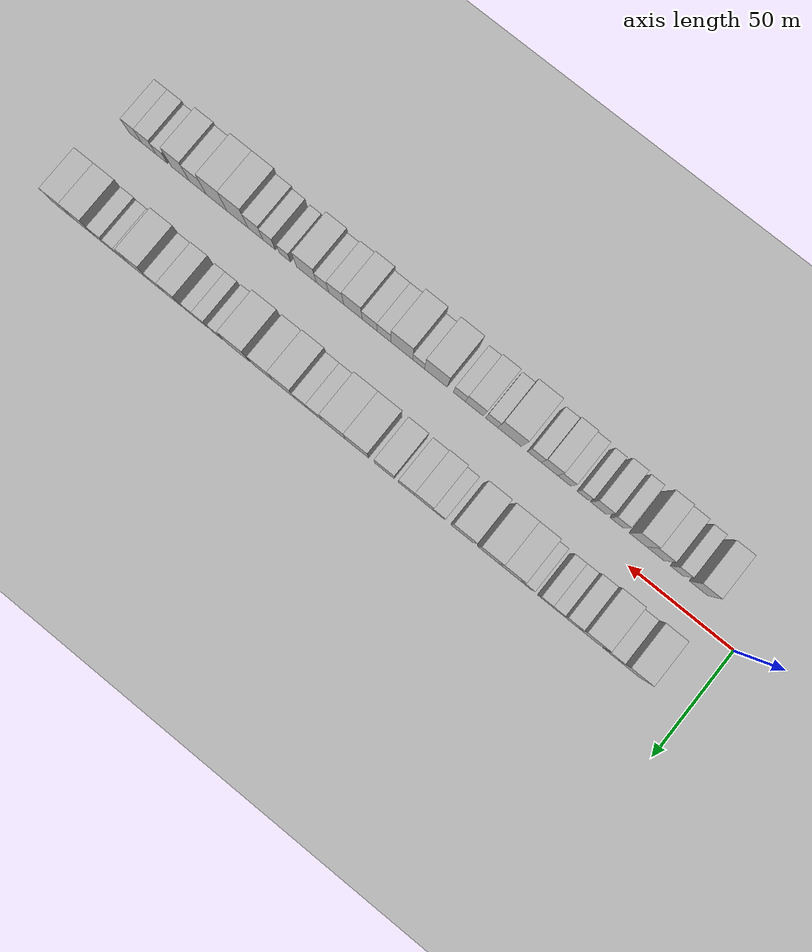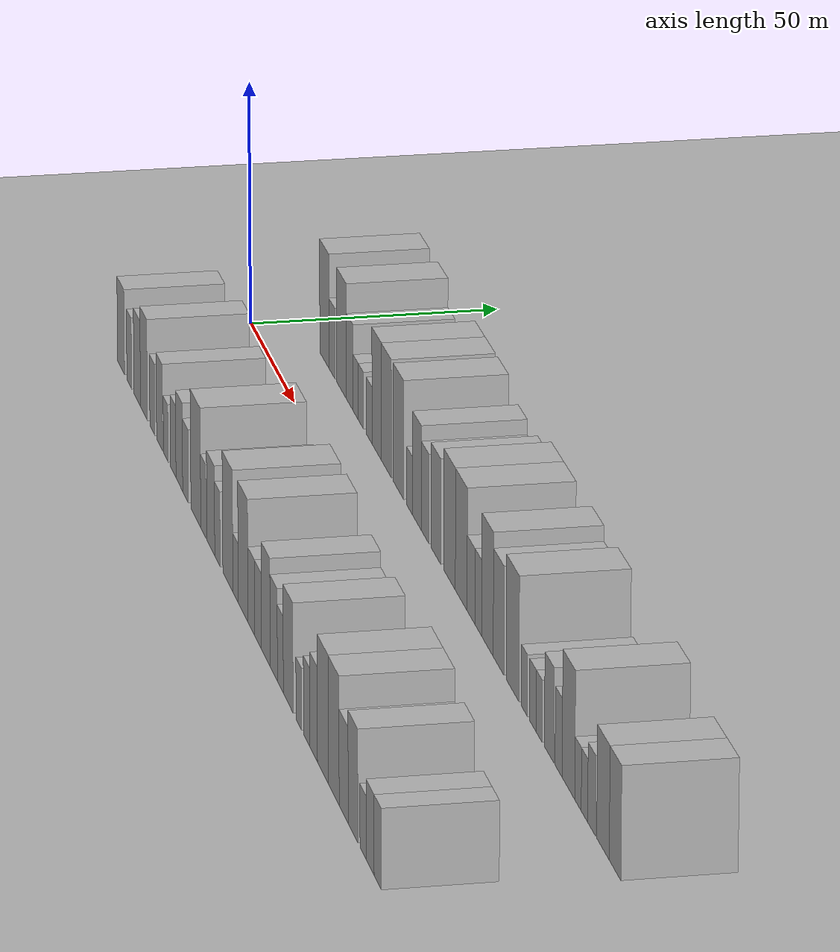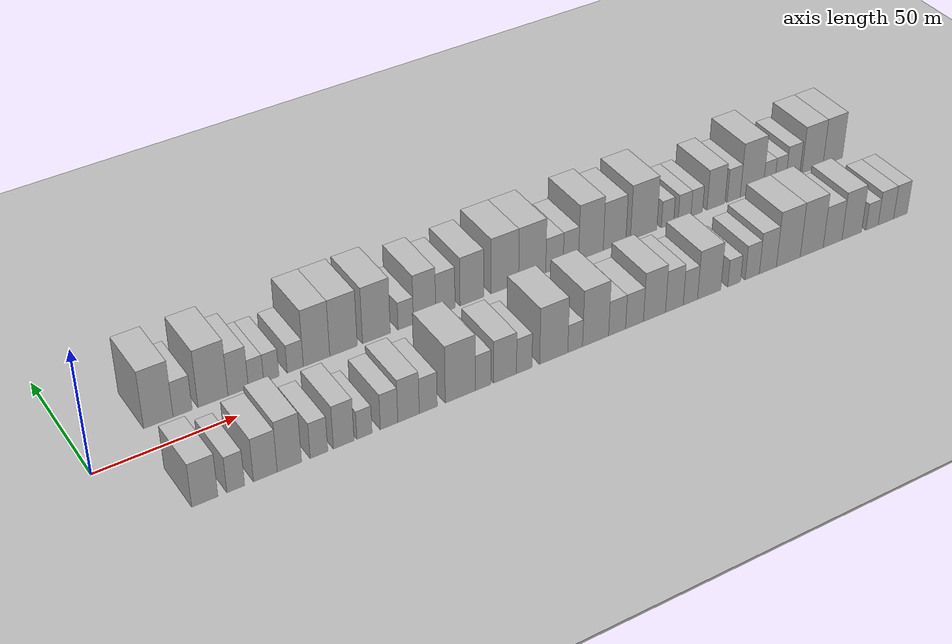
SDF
<?xml version="1.0" encoding="utf-8"?>

<sdf version="1.6">

   <world name="default">

      <gui fullscreen="0">

         <camera name="user_camera">

            <pose>-15 0 4.57585 0 0 0</pose>

            <view_controller>orbit</view_controller>

         </camera>

      </gui>

      <scene>

         <sky>

           <clouds>

             <speed>12</speed>

           </clouds>

         </sky>

         <ambient>0.4 0.4 0.4 1</ambient>

         <background>0.7 0.7 0.7 1</background>

         <shadows>1</shadows>

      </scene>

      <gravity>0 0 -9.8066</gravity>

      <magnetic_field>6e-06 2.3e-05 -4.2e-05</magnetic_field>

      <physics default="0" name="default_physics" type="ode">

         <ode>

            <solver>

               <type>quick</type>

               <iters>10</iters>

               <sor>1.0</sor>

               <use_dynamic_moi_rescaling>0</use_dynamic_moi_rescaling>

            </solver>

            <constraints>

               <cfm>0</cfm>

               <erp>0.2</erp>

               <contact_max_correcting_vel>100</contact_max_correcting_vel>

               <contact_surface_layer>0.001</contact_surface_layer>

            </constraints>

         </ode>

         <max_step_size>0.004</max_step_size>

         <real_time_factor>1</real_time_factor>

         <real_time_update_rate>250</real_time_update_rate>

      </physics>

      <light name="sun" type="directional">

         <cast_shadows>1</cast_shadows>

         <pose>0 0 10 0 0 0</pose>

         <diffuse>0.8 0.8 0.8 1</diffuse>

         <specular>0.2 0.2 0.2 1</specular>

         <attenuation>

            <range>1000</range>

            <constant>0.9</constant>

            <linear>0.01</linear>

            <quadratic>0.001</quadratic>

         </attenuation>

         <direction>-0.5 0.1 -0.9</direction>

      </light>

      <include>

         <name>ground_plane_1</name>

         <uri>model://HANNAS_ground_plane</uri>

         <pose>0 0 0  0 0 0</pose>

      </include>

      <include>

         <name>ground_plane_2</name>

         <uri>model://HANNAS_ground_plane</uri>

         <pose>100 0 0  0 0 0</pose>

      </include>

      <model name="building_1">

         <static>1</static>

         <pose frame="">27.1083 20.0000 0 0.000000 0.000000 1.570796</pose>

         <link name="link">

            <pose frame="">0 0 12.00 0 0 0</pose>

            <collision name="collision">

               <geometry>

                  <box>

                     <size>20.0000 10.2167 24.0000</size>

                  </box>

               </geometry>

               <max_contacts>10</max_contacts>

               <surface>

                  <contact>

                     <ode/>

                  </contact>

                  <bounce/>

                  <friction>

                     <torsional>

                        <ode/>

                     </torsional>

                     <ode/>

                  </friction>

               </surface>

            </collision>

            <visual name="visual">

               <cast_shadows>0</cast_shadows>

               <geometry>

                  <box>

                     <size>20.0000 10.2167 24.0000</size>

                  </box>

               </geometry>

               <material>

                  <script>

                     <uri>model://HANNAS_wall/materials/scripts</uri>

                     <uri>model://HANNAS_wall/materials/textures</uri>

                     <name>vrc/HANNAS_wall</name>

                  </script>

               </material>

            </visual>

            <self_collide>0</self_collide>

            <enable_wind>0</enable_wind>

            <kinematic>0</kinematic>

         </link>

      </model>

      <model name="building_2">

         <static>1</static>

         <pose frame="">35.5468 20.0000 0 0.000000 0.000000 1.570796</pose>

         <link name="link">

            <pose frame="">0 0 7.50 0 0 0</pose>

            <collision name="collision">

               <geometry>

                  <box>

                     <size>20.0000 6.6602 15.0000</size>

                  </box>

               </geometry>

               <max_contacts>10</max_contacts>

               <surface>

                  <contact>

                     <ode/>

                  </contact>

                  <bounce/>

                  <friction>

                     <torsional>

                        <ode/>

                     </torsional>

                     <ode/>

                  </friction>

               </surface>

            </collision>

            <visual name="visual">

               <cast_shadows>0</cast_shadows>

               <geometry>

                  <box>

                     <size>20.0000 6.6602 15.0000</size>

                  </box>

               </geometry>

               <material>

                  <script>

                     <uri>model://HANNAS_wall/materials/scripts</uri>

                     <uri>model://HANNAS_wall/materials/textures</uri>

                     <name>vrc/HANNAS_wall</name>

                  </script>

               </material>

            </visual>

            <self_collide>0</self_collide>

            <enable_wind>0</enable_wind>

            <kinematic>0</kinematic>

         </link>

      </model>

      <model name="building_3">

         <static>1</static>

         <pose frame="">46.1967 20.0000 0 0.000000 0.000000 1.570796</pose>

         <link name="link">

            <pose frame="">0 0 12.00 0 0 0</pose>

            <collision name="collision">

               <geometry>

                  <box>

                     <size>20.0000 10.6396 24.0000</size>

                  </box>

               </geometry>

               <max_contacts>10</max_contacts>

               <surface>

                  <contact>

                     <ode/>

                  </contact>

                  <bounce/>

                  <friction>

                     <torsional>

                        <ode/>

                     </torsional>

                     <ode/>

                  </friction>

               </surface>

            </collision>

            <visual name="visual">

               <cast_shadows>0</cast_shadows>

               <geometry>

                  <box>

                     <size>20.0000 10.6396 24.0000</size>

                  </box>

               </geometry>

               <material>

                  <script>

                     <uri>model://HANNAS_wall/materials/scripts</uri>

                     <uri>model://HANNAS_wall/materials/textures</uri>

                     <name>vrc/HANNAS_wall</name>

                  </script>

               </material>

            </visual>

            <self_collide>0</self_collide>

            <enable_wind>0</enable_wind>

            <kinematic>0</kinematic>

         </link>

      </model>

      <model name="building_4">

         <static>1</static>

         <pose frame="">55.1658 20.0000 0 0.000000 0.000000 1.570796</pose>

         <link name="link">

            <pose frame="">0 0 9.00 0 0 0</pose>

            <collision name="collision">

               <geometry>

                  <box>

                     <size>20.0000 7.2986 18.0000</size>

                  </box>

               </geometry>

               <max_contacts>10</max_contacts>

               <surface>

                  <contact>

                     <ode/>

                  </contact>

                  <bounce/>

                  <friction>

                     <torsional>

                        <ode/>

                     </torsional>

                     <ode/>

                  </friction>

               </surface>

            </collision>

            <visual name="visual">

               <cast_shadows>0</cast_shadows>

               <geometry>

                  <box>

                     <size>20.0000 7.2986 18.0000</size>

                  </box>

               </geometry>

               <material>

                  <script>

                     <uri>model://HANNAS_wall/materials/scripts</uri>

                     <uri>model://HANNAS_wall/materials/textures</uri>

                     <name>vrc/HANNAS_wall</name>

                  </script>

               </material>

            </visual>

            <self_collide>0</self_collide>

            <enable_wind>0</enable_wind>

            <kinematic>0</kinematic>

         </link>

      </model>

      <model name="building_5">

         <static>1</static>

         <pose frame="">61.5858 20.0000 0 0.000000 0.000000 1.570796</pose>

         <link name="link">

            <pose frame="">0 0 6.00 0 0 0</pose>

            <collision name="collision">

               <geometry>

                  <box>

                     <size>20.0000 5.5414 12.0000</size>

                  </box>

               </geometry>

               <max_contacts>10</max_contacts>

               <surface>

                  <contact>

                     <ode/>

                  </contact>

                  <bounce/>

                  <friction>

                     <torsional>

                        <ode/>

                     </torsional>

                     <ode/>

                  </friction>

               </surface>

            </collision>

            <visual name="visual">

               <cast_shadows>0</cast_shadows>

               <geometry>

                  <box>

                     <size>20.0000 5.5414 12.0000</size>

                  </box>

               </geometry>

               <material>

                  <script>

                     <uri>model://HANNAS_wall/materials/scripts</uri>

                     <uri>model://HANNAS_wall/materials/textures</uri>

                     <name>vrc/HANNAS_wall</name>

                  </script>

               </material>

            </visual>

            <self_collide>0</self_collide>

            <enable_wind>0</enable_wind>

            <kinematic>0</kinematic>

         </link>

      </model>

      <model name="building_6">

         <static>1</static>

         <pose frame="">67.1333 20.0000 0 0.000000 0.000000 1.570796</pose>

         <link name="link">

            <pose frame="">0 0 6.00 0 0 0</pose>

            <collision name="collision">

               <geometry>

                  <box>

                     <size>20.0000 5.5535 12.0000</size>

                  </box>

               </geometry>

               <max_contacts>10</max_contacts>

               <surface>

                  <contact>

                     <ode/>

                  </contact>

                  <bounce/>

                  <friction>

                     <torsional>

                        <ode/>

                     </torsional>

                     <ode/>

                  </friction>

               </surface>

            </collision>

            <visual name="visual">

               <cast_shadows>0</cast_shadows>

               <geometry>

                  <box>

                     <size>20.0000 5.5535 12.0000</size>

                  </box>

               </geometry>

               <material>

                  <script>

                     <uri>model://HANNAS_wall/materials/scripts</uri>

                     <uri>model://HANNAS_wall/materials/textures</uri>

                     <name>vrc/HANNAS_wall</name>

                  </script>

               </material>

            </visual>

            <self_collide>0</self_collide>

            <enable_wind>0</enable_wind>

            <kinematic>0</kinematic>

         </link>

      </model>

      <model name="building_7">

         <static>1</static>

         <pose frame="">75.8970 20.0000 0 0.000000 0.000000 1.570796</pose>

         <link name="link">

            <pose frame="">0 0 6.00 0 0 0</pose>

            <collision name="collision">

               <geometry>

                  <box>

                     <size>20.0000 5.9740 12.0000</size>

                  </box>

               </geometry>

               <max_contacts>10</max_contacts>

               <surface>

                  <contact>

                     <ode/>

                  </contact>

                  <bounce/>

                  <friction>

                     <torsional>

                        <ode/>

                     </torsional>

                     <ode/>

                  </friction>

               </surface>

            </collision>

            <visual name="visual">

               <cast_shadows>0</cast_shadows>

               <geometry>

                  <box>

                     <size>20.0000 5.9740 12.0000</size>

                  </box>

               </geometry>

               <material>

                  <script>

                     <uri>model://HANNAS_wall/materials/scripts</uri>

                     <uri>model://HANNAS_wall/materials/textures</uri>

                     <name>vrc/HANNAS_wall</name>

                  </script>

               </material>

            </visual>

            <self_collide>0</self_collide>

            <enable_wind>0</enable_wind>

            <kinematic>0</kinematic>

         </link>

      </model>

      <model name="building_8">

         <static>1</static>

         <pose frame="">83.8002 20.0000 0 0.000000 0.000000 1.570796</pose>

         <link name="link">

            <pose frame="">0 0 12.00 0 0 0</pose>

            <collision name="collision">

               <geometry>

                  <box>

                     <size>20.0000 9.8323 24.0000</size>

                  </box>

               </geometry>

               <max_contacts>10</max_contacts>

               <surface>

                  <contact>

                     <ode/>

                  </contact>

                  <bounce/>

                  <friction>

                     <torsional>

                        <ode/>

                     </torsional>

                     <ode/>

                  </friction>

               </surface>

            </collision>

            <visual name="visual">

               <cast_shadows>0</cast_shadows>

               <geometry>

                  <box>

                     <size>20.0000 9.8323 24.0000</size>

                  </box>

               </geometry>

               <material>

                  <script>

                     <uri>model://HANNAS_wall/materials/scripts</uri>

                     <uri>model://HANNAS_wall/materials/textures</uri>

                     <name>vrc/HANNAS_wall</name>

                  </script>

               </material>

            </visual>

            <self_collide>0</self_collide>

            <enable_wind>0</enable_wind>

            <kinematic>0</kinematic>

         </link>

      </model>

      <model name="building_9">

         <static>1</static>

         <pose frame="">93.9026 20.0000 0 0.000000 0.000000 1.570796</pose>

         <link name="link">

            <pose frame="">0 0 12.00 0 0 0</pose>

            <collision name="collision">

               <geometry>

                  <box>

                     <size>20.0000 10.3726 24.0000</size>

                  </box>

               </geometry>

               <max_contacts>10</max_contacts>

               <surface>

                  <contact>

                     <ode/>

                  </contact>

                  <bounce/>

                  <friction>

                     <torsional>

                        <ode/>

                     </torsional>

                     <ode/>

                  </friction>

               </surface>

            </collision>

            <visual name="visual">

               <cast_shadows>0</cast_shadows>

               <geometry>

                  <box>

                     <size>20.0000 10.3726 24.0000</size>

                  </box>

               </geometry>

               <material>

                  <script>

                     <uri>model://HANNAS_wall/materials/scripts</uri>

                     <uri>model://HANNAS_wall/materials/textures</uri>

                     <name>vrc/HANNAS_wall</name>

                  </script>

               </material>

            </visual>

            <self_collide>0</self_collide>

            <enable_wind>0</enable_wind>

            <kinematic>0</kinematic>

         </link>

      </model>

      <model name="building_10">

         <static>1</static>

         <pose frame="">106.4162 20.0000 0 0.000000 0.000000 1.570796</pose>

         <link name="link">

            <pose frame="">0 0 12.00 0 0 0</pose>

            <collision name="collision">

               <geometry>

                  <box>

                     <size>20.0000 10.6545 24.0000</size>

                  </box>

               </geometry>

               <max_contacts>10</max_contacts>

               <surface>

                  <contact>

                     <ode/>

                  </contact>

                  <bounce/>

                  <friction>

                     <torsional>

                        <ode/>

                     </torsional>

                     <ode/>

                  </friction>

               </surface>

            </collision>

            <visual name="visual">

               <cast_shadows>0</cast_shadows>

               <geometry>

                  <box>

                     <size>20.0000 10.6545 24.0000</size>

                  </box>

               </geometry>

               <material>

                  <script>

                     <uri>model://HANNAS_wall/materials/scripts</uri>

                     <uri>model://HANNAS_wall/materials/textures</uri>

                     <name>vrc/HANNAS_wall</name>

                  </script>

               </material>

            </visual>

            <self_collide>0</self_collide>

            <enable_wind>0</enable_wind>

            <kinematic>0</kinematic>

         </link>

      </model>

      <model name="building_11">

         <static>1</static>

         <pose frame="">117.7329 20.0000 0 0.000000 0.000000 1.570796</pose>

         <link name="link">

            <pose frame="">0 0 6.00 0 0 0</pose>

            <collision name="collision">

               <geometry>

                  <box>

                     <size>20.0000 5.9790 12.0000</size>

                  </box>

               </geometry>

               <max_contacts>10</max_contacts>

               <surface>

                  <contact>

                     <ode/>

                  </contact>

                  <bounce/>

                  <friction>

                     <torsional>

                        <ode/>

                     </torsional>

                     <ode/>

                  </friction>

               </surface>

            </collision>

            <visual name="visual">

               <cast_shadows>0</cast_shadows>

               <geometry>

                  <box>

                     <size>20.0000 5.9790 12.0000</size>

                  </box>

               </geometry>

               <material>

                  <script>

                     <uri>model://HANNAS_wall/materials/scripts</uri>

                     <uri>model://HANNAS_wall/materials/textures</uri>

                     <name>vrc/HANNAS_wall</name>

                  </script>

               </material>

            </visual>

            <self_collide>0</self_collide>

            <enable_wind>0</enable_wind>

            <kinematic>0</kinematic>

         </link>

      </model>

      <model name="building_12">

         <static>1</static>

         <pose frame="">125.1094 20.0000 0 0.000000 0.000000 1.570796</pose>

         <link name="link">

            <pose frame="">0 0 10.50 0 0 0</pose>

            <collision name="collision">

               <geometry>

                  <box>

                     <size>20.0000 8.7740 21.0000</size>

                  </box>

               </geometry>

               <max_contacts>10</max_contacts>

               <surface>

                  <contact>

                     <ode/>

                  </contact>

                  <bounce/>

                  <friction>

                     <torsional>

                        <ode/>

                     </torsional>

                     <ode/>

                  </friction>

               </surface>

            </collision>

            <visual name="visual">

               <cast_shadows>0</cast_shadows>

               <geometry>

                  <box>

                     <size>20.0000 8.7740 21.0000</size>

                  </box>

               </geometry>

               <material>

                  <script>

                     <uri>model://HANNAS_wall/materials/scripts</uri>

                     <uri>model://HANNAS_wall/materials/textures</uri>

                     <name>vrc/HANNAS_wall</name>

                  </script>

               </material>

            </visual>

            <self_collide>0</self_collide>

            <enable_wind>0</enable_wind>

            <kinematic>0</kinematic>

         </link>

      </model>

      <model name="building_13">

         <static>1</static>

         <pose frame="">133.3089 20.0000 0 0.000000 0.000000 1.570796</pose>

         <link name="link">

            <pose frame="">0 0 9.00 0 0 0</pose>

            <collision name="collision">

               <geometry>

                  <box>

                     <size>20.0000 7.6250 18.0000</size>

                  </box>

               </geometry>

               <max_contacts>10</max_contacts>

               <surface>

                  <contact>

                     <ode/>

                  </contact>

                  <bounce/>

                  <friction>

                     <torsional>

                        <ode/>

                     </torsional>

                     <ode/>

                  </friction>

               </surface>

            </collision>

            <visual name="visual">

               <cast_shadows>0</cast_shadows>

               <geometry>

                  <box>

                     <size>20.0000 7.6250 18.0000</size>

                  </box>

               </geometry>

               <material>

                  <script>

                     <uri>model://HANNAS_wall/materials/scripts</uri>

                     <uri>model://HANNAS_wall/materials/textures</uri>

                     <name>vrc/HANNAS_wall</name>

                  </script>

               </material>

            </visual>

            <self_collide>0</self_collide>

            <enable_wind>0</enable_wind>

            <kinematic>0</kinematic>

         </link>

      </model>

      <model name="building_14">

         <static>1</static>

         <pose frame="">143.8704 20.0000 0 0.000000 0.000000 1.570796</pose>

         <link name="link">

            <pose frame="">0 0 10.50 0 0 0</pose>

            <collision name="collision">

               <geometry>

                  <box>

                     <size>20.0000 9.4981 21.0000</size>

                  </box>

               </geometry>

               <max_contacts>10</max_contacts>

               <surface>

                  <contact>

                     <ode/>

                  </contact>

                  <bounce/>

                  <friction>

                     <torsional>

                        <ode/>

                     </torsional>

                     <ode/>

                  </friction>

               </surface>

            </collision>

            <visual name="visual">

               <cast_shadows>0</cast_shadows>

               <geometry>

                  <box>

                     <size>20.0000 9.4981 21.0000</size>

                  </box>

               </geometry>

               <material>

                  <script>

                     <uri>model://HANNAS_wall/materials/scripts</uri>

                     <uri>model://HANNAS_wall/materials/textures</uri>

                     <name>vrc/HANNAS_wall</name>

                  </script>

               </material>

            </visual>

            <self_collide>0</self_collide>

            <enable_wind>0</enable_wind>

            <kinematic>0</kinematic>

         </link>

      </model>

      <model name="building_15">

         <static>1</static>

         <pose frame="">157.2429 20.0000 0 0.000000 0.000000 1.570796</pose>

         <link name="link">

            <pose frame="">0 0 12.00 0 0 0</pose>

            <collision name="collision">

               <geometry>

                  <box>

                     <size>20.0000 11.2469 24.0000</size>

                  </box>

               </geometry>

               <max_contacts>10</max_contacts>

               <surface>

                  <contact>

                     <ode/>

                  </contact>

                  <bounce/>

                  <friction>

                     <torsional>

                        <ode/>

                     </torsional>

                     <ode/>

                  </friction>

               </surface>

            </collision>

            <visual name="visual">

               <cast_shadows>0</cast_shadows>

               <geometry>

                  <box>

                     <size>20.0000 11.2469 24.0000</size>

                  </box>

               </geometry>

               <material>

                  <script>

                     <uri>model://HANNAS_wall/materials/scripts</uri>

                     <uri>model://HANNAS_wall/materials/textures</uri>

                     <name>vrc/HANNAS_wall</name>

                  </script>

               </material>

            </visual>

            <self_collide>0</self_collide>

            <enable_wind>0</enable_wind>

            <kinematic>0</kinematic>

         </link>

      </model>

      <model name="building_16">

         <static>1</static>

         <pose frame="">168.4958 20.0000 0 0.000000 0.000000 1.570796</pose>

         <link name="link">

            <pose frame="">0 0 12.00 0 0 0</pose>

            <collision name="collision">

               <geometry>

                  <box>

                     <size>20.0000 11.2589 24.0000</size>

                  </box>

               </geometry>

               <max_contacts>10</max_contacts>

               <surface>

                  <contact>

                     <ode/>

                  </contact>

                  <bounce/>

                  <friction>

                     <torsional>

                        <ode/>

                     </torsional>

                     <ode/>

                  </friction>

               </surface>

            </collision>

            <visual name="visual">

               <cast_shadows>0</cast_shadows>

               <geometry>

                  <box>

                     <size>20.0000 11.2589 24.0000</size>

                  </box>

               </geometry>

               <material>

                  <script>

                     <uri>model://HANNAS_wall/materials/scripts</uri>

                     <uri>model://HANNAS_wall/materials/textures</uri>

                     <name>vrc/HANNAS_wall</name>

                  </script>

               </material>

            </visual>

            <self_collide>0</self_collide>

            <enable_wind>0</enable_wind>

            <kinematic>0</kinematic>

         </link>

      </model>

      <model name="building_17">

         <static>1</static>

         <pose frame="">177.7843 20.0000 0 0.000000 0.000000 1.570796</pose>

         <link name="link">

            <pose frame="">0 0 7.50 0 0 0</pose>

            <collision name="collision">

               <geometry>

                  <box>

                     <size>20.0000 7.3181 15.0000</size>

                  </box>

               </geometry>

               <max_contacts>10</max_contacts>

               <surface>

                  <contact>

                     <ode/>

                  </contact>

                  <bounce/>

                  <friction>

                     <torsional>

                        <ode/>

                     </torsional>

                     <ode/>

                  </friction>

               </surface>

            </collision>

            <visual name="visual">

               <cast_shadows>0</cast_shadows>

               <geometry>

                  <box>

                     <size>20.0000 7.3181 15.0000</size>

                  </box>

               </geometry>

               <material>

                  <script>

                     <uri>model://HANNAS_wall/materials/scripts</uri>

                     <uri>model://HANNAS_wall/materials/textures</uri>

                     <name>vrc/HANNAS_wall</name>

                  </script>

               </material>

            </visual>

            <self_collide>0</self_collide>

            <enable_wind>0</enable_wind>

            <kinematic>0</kinematic>

         </link>

      </model>

      <model name="building_18">

         <static>1</static>

         <pose frame="">184.6922 20.0000 0 0.000000 0.000000 1.570796</pose>

         <link name="link">

            <pose frame="">0 0 7.50 0 0 0</pose>

            <collision name="collision">

               <geometry>

                  <box>

                     <size>20.0000 6.4976 15.0000</size>

                  </box>

               </geometry>

               <max_contacts>10</max_contacts>

               <surface>

                  <contact>

                     <ode/>

                  </contact>

                  <bounce/>

                  <friction>

                     <torsional>

                        <ode/>

                     </torsional>

                     <ode/>

                  </friction>

               </surface>

            </collision>

            <visual name="visual">

               <cast_shadows>0</cast_shadows>

               <geometry>

                  <box>

                     <size>20.0000 6.4976 15.0000</size>

                  </box>

               </geometry>

               <material>

                  <script>

                     <uri>model://HANNAS_wall/materials/scripts</uri>

                     <uri>model://HANNAS_wall/materials/textures</uri>

                     <name>vrc/HANNAS_wall</name>

                  </script>

               </material>

            </visual>

            <self_collide>0</self_collide>

            <enable_wind>0</enable_wind>

            <kinematic>0</kinematic>

         </link>

      </model>

      <model name="building_19">

         <static>1</static>

         <pose frame="">193.2254 20.0000 0 0.000000 0.000000 1.570796</pose>

         <link name="link">

            <pose frame="">0 0 12.00 0 0 0</pose>

            <collision name="collision">

               <geometry>

                  <box>

                     <size>20.0000 10.5688 24.0000</size>

                  </box>

               </geometry>

               <max_contacts>10</max_contacts>

               <surface>

                  <contact>

                     <ode/>

                  </contact>

                  <bounce/>

                  <friction>

                     <torsional>

                        <ode/>

                     </torsional>

                     <ode/>

                  </friction>

               </surface>

            </collision>

            <visual name="visual">

               <cast_shadows>0</cast_shadows>

               <geometry>

                  <box>

                     <size>20.0000 10.5688 24.0000</size>

                  </box>

               </geometry>

               <material>

                  <script>

                     <uri>model://HANNAS_wall/materials/scripts</uri>

                     <uri>model://HANNAS_wall/materials/textures</uri>

                     <name>vrc/HANNAS_wall</name>

                  </script>

               </material>

            </visual>

            <self_collide>0</self_collide>

            <enable_wind>0</enable_wind>

            <kinematic>0</kinematic>

         </link>

      </model>

      <model name="building_20">

         <static>1</static>

         <pose frame="">203.3958 20.0000 0 0.000000 0.000000 1.570796</pose>

         <link name="link">

            <pose frame="">0 0 10.50 0 0 0</pose>

            <collision name="collision">

               <geometry>

                  <box>

                     <size>20.0000 9.7721 21.0000</size>

                  </box>

               </geometry>

               <max_contacts>10</max_contacts>

               <surface>

                  <contact>

                     <ode/>

                  </contact>

                  <bounce/>

                  <friction>

                     <torsional>

                        <ode/>

                     </torsional>

                     <ode/>

                  </friction>

               </surface>

            </collision>

            <visual name="visual">

               <cast_shadows>0</cast_shadows>

               <geometry>

                  <box>

                     <size>20.0000 9.7721 21.0000</size>

                  </box>

               </geometry>

               <material>

                  <script>

                     <uri>model://HANNAS_wall/materials/scripts</uri>

                     <uri>model://HANNAS_wall/materials/textures</uri>

                     <name>vrc/HANNAS_wall</name>

                  </script>

               </material>

            </visual>

            <self_collide>0</self_collide>

            <enable_wind>0</enable_wind>

            <kinematic>0</kinematic>

         </link>

      </model>

      <model name="building_21">

         <static>1</static>

         <pose frame="">216.1008 20.0000 0 0.000000 0.000000 1.570796</pose>

         <link name="link">

            <pose frame="">0 0 12.00 0 0 0</pose>

            <collision name="collision">

               <geometry>

                  <box>

                     <size>20.0000 11.6379 24.0000</size>

                  </box>

               </geometry>

               <max_contacts>10</max_contacts>

               <surface>

                  <contact>

                     <ode/>

                  </contact>

                  <bounce/>

                  <friction>

                     <torsional>

                        <ode/>

                     </torsional>

                     <ode/>

                  </friction>

               </surface>

            </collision>

            <visual name="visual">

               <cast_shadows>0</cast_shadows>

               <geometry>

                  <box>

                     <size>20.0000 11.6379 24.0000</size>

                  </box>

               </geometry>

               <material>

                  <script>

                     <uri>model://HANNAS_wall/materials/scripts</uri>

                     <uri>model://HANNAS_wall/materials/textures</uri>

                     <name>vrc/HANNAS_wall</name>

                  </script>

               </material>

            </visual>

            <self_collide>0</self_collide>

            <enable_wind>0</enable_wind>

            <kinematic>0</kinematic>

         </link>

      </model>

      <model name="building_22">

         <static>1</static>

         <pose frame="">226.6469 20.0000 0 0.000000 0.000000 1.570796</pose>

         <link name="link">

            <pose frame="">0 0 6.00 0 0 0</pose>

            <collision name="collision">

               <geometry>

                  <box>

                     <size>20.0000 5.4542 12.0000</size>

                  </box>

               </geometry>

               <max_contacts>10</max_contacts>

               <surface>

                  <contact>

                     <ode/>

                  </contact>

                  <bounce/>

                  <friction>

                     <torsional>

                        <ode/>

                     </torsional>

                     <ode/>

                  </friction>

               </surface>

            </collision>

            <visual name="visual">

               <cast_shadows>0</cast_shadows>

               <geometry>

                  <box>

                     <size>20.0000 5.4542 12.0000</size>

                  </box>

               </geometry>

               <material>

                  <script>

                     <uri>model://HANNAS_wall/materials/scripts</uri>

                     <uri>model://HANNAS_wall/materials/textures</uri>

                     <name>vrc/HANNAS_wall</name>

                  </script>

               </material>

            </visual>

            <self_collide>0</self_collide>

            <enable_wind>0</enable_wind>

            <kinematic>0</kinematic>

         </link>

      </model>

      <model name="building_23">

         <static>1</static>

         <pose frame="">234.2700 20.0000 0 0.000000 0.000000 1.570796</pose>

         <link name="link">

            <pose frame="">0 0 6.00 0 0 0</pose>

            <collision name="collision">

               <geometry>

                  <box>

                     <size>20.0000 5.7919 12.0000</size>

                  </box>

               </geometry>

               <max_contacts>10</max_contacts>

               <surface>

                  <contact>

                     <ode/>

                  </contact>

                  <bounce/>

                  <friction>

                     <torsional>

                        <ode/>

                     </torsional>

                     <ode/>

                  </friction>

               </surface>

            </collision>

            <visual name="visual">

               <cast_shadows>0</cast_shadows>

               <geometry>

                  <box>

                     <size>20.0000 5.7919 12.0000</size>

                  </box>

               </geometry>

               <material>

                  <script>

                     <uri>model://HANNAS_wall/materials/scripts</uri>

                     <uri>model://HANNAS_wall/materials/textures</uri>

                     <name>vrc/HANNAS_wall</name>

                  </script>

               </material>

            </visual>

            <self_collide>0</self_collide>

            <enable_wind>0</enable_wind>

            <kinematic>0</kinematic>

         </link>

      </model>

      <model name="building_24">

         <static>1</static>

         <pose frame="">239.7805 20.0000 0 0.000000 0.000000 1.570796</pose>

         <link name="link">

            <pose frame="">0 0 6.00 0 0 0</pose>

            <collision name="collision">

               <geometry>

                  <box>

                     <size>20.0000 5.2292 12.0000</size>

                  </box>

               </geometry>

               <max_contacts>10</max_contacts>

               <surface>

                  <contact>

                     <ode/>

                  </contact>

                  <bounce/>

                  <friction>

                     <torsional>

                        <ode/>

                     </torsional>

                     <ode/>

                  </friction>

               </surface>

            </collision>

            <visual name="visual">

               <cast_shadows>0</cast_shadows>

               <geometry>

                  <box>

                     <size>20.0000 5.2292 12.0000</size>

                  </box>

               </geometry>

               <material>

                  <script>

                     <uri>model://HANNAS_wall/materials/scripts</uri>

                     <uri>model://HANNAS_wall/materials/textures</uri>

                     <name>vrc/HANNAS_wall</name>

                  </script>

               </material>

            </visual>

            <self_collide>0</self_collide>

            <enable_wind>0</enable_wind>

            <kinematic>0</kinematic>

         </link>

      </model>

      <model name="building_25">

         <static>1</static>

         <pose frame="">248.5028 20.0000 0 0.000000 0.000000 1.570796</pose>

         <link name="link">

            <pose frame="">0 0 9.00 0 0 0</pose>

            <collision name="collision">

               <geometry>

                  <box>

                     <size>20.0000 8.2153 18.0000</size>

                  </box>

               </geometry>

               <max_contacts>10</max_contacts>

               <surface>

                  <contact>

                     <ode/>

                  </contact>

                  <bounce/>

                  <friction>

                     <torsional>

                        <ode/>

                     </torsional>

                     <ode/>

                  </friction>

               </surface>

            </collision>

            <visual name="visual">

               <cast_shadows>0</cast_shadows>

               <geometry>

                  <box>

                     <size>20.0000 8.2153 18.0000</size>

                  </box>

               </geometry>

               <material>

                  <script>

                     <uri>model://HANNAS_wall/materials/scripts</uri>

                     <uri>model://HANNAS_wall/materials/textures</uri>

                     <name>vrc/HANNAS_wall</name>

                  </script>

               </material>

            </visual>

            <self_collide>0</self_collide>

            <enable_wind>0</enable_wind>

            <kinematic>0</kinematic>

         </link>

      </model>

      <model name="building_26">

         <static>1</static>

         <pose frame="">256.6438 20.0000 0 0.000000 0.000000 1.570796</pose>

         <link name="link">

            <pose frame="">0 0 7.50 0 0 0</pose>

            <collision name="collision">

               <geometry>

                  <box>

                     <size>20.0000 6.0667 15.0000</size>

                  </box>

               </geometry>

               <max_contacts>10</max_contacts>

               <surface>

                  <contact>

                     <ode/>

                  </contact>

                  <bounce/>

                  <friction>

                     <torsional>

                        <ode/>

                     </torsional>

                     <ode/>

                  </friction>

               </surface>

            </collision>

            <visual name="visual">

               <cast_shadows>0</cast_shadows>

               <geometry>

                  <box>

                     <size>20.0000 6.0667 15.0000</size>

                  </box>

               </geometry>

               <material>

                  <script>

                     <uri>model://HANNAS_wall/materials/scripts</uri>

                     <uri>model://HANNAS_wall/materials/textures</uri>

                     <name>vrc/HANNAS_wall</name>

                  </script>

               </material>

            </visual>

            <self_collide>0</self_collide>

            <enable_wind>0</enable_wind>

            <kinematic>0</kinematic>

         </link>

      </model>

      <model name="building_27">

         <static>1</static>

         <pose frame="">265.0303 20.0000 0 0.000000 0.000000 1.570796</pose>

         <link name="link">

            <pose frame="">0 0 12.00 0 0 0</pose>

            <collision name="collision">

               <geometry>

                  <box>

                     <size>20.0000 10.7064 24.0000</size>

                  </box>

               </geometry>

               <max_contacts>10</max_contacts>

               <surface>

                  <contact>

                     <ode/>

                  </contact>

                  <bounce/>

                  <friction>

                     <torsional>

                        <ode/>

                     </torsional>

                     <ode/>

                  </friction>

               </surface>

            </collision>

            <visual name="visual">

               <cast_shadows>0</cast_shadows>

               <geometry>

                  <box>

                     <size>20.0000 10.7064 24.0000</size>

                  </box>

               </geometry>

               <material>

                  <script>

                     <uri>model://HANNAS_wall/materials/scripts</uri>

                     <uri>model://HANNAS_wall/materials/textures</uri>

                     <name>vrc/HANNAS_wall</name>

                  </script>

               </material>

            </visual>

            <self_collide>0</self_collide>

            <enable_wind>0</enable_wind>

            <kinematic>0</kinematic>

         </link>

      </model>

      <model name="building_28">

         <static>1</static>

         <pose frame="">273.0879 20.0000 0 0.000000 0.000000 1.570796</pose>

         <link name="link">

            <pose frame="">0 0 6.00 0 0 0</pose>

            <collision name="collision">

               <geometry>

                  <box>

                     <size>20.0000 5.4087 12.0000</size>

                  </box>

               </geometry>

               <max_contacts>10</max_contacts>

               <surface>

                  <contact>

                     <ode/>

                  </contact>

                  <bounce/>

                  <friction>

                     <torsional>

                        <ode/>

                     </torsional>

                     <ode/>

                  </friction>

               </surface>

            </collision>

            <visual name="visual">

               <cast_shadows>0</cast_shadows>

               <geometry>

                  <box>

                     <size>20.0000 5.4087 12.0000</size>

                  </box>

               </geometry>

               <material>

                  <script>

                     <uri>model://HANNAS_wall/materials/scripts</uri>

                     <uri>model://HANNAS_wall/materials/textures</uri>

                     <name>vrc/HANNAS_wall</name>

                  </script>

               </material>

            </visual>

            <self_collide>0</self_collide>

            <enable_wind>0</enable_wind>

            <kinematic>0</kinematic>

         </link>

      </model>

      <model name="building_29">

         <static>1</static>

         <pose frame="">278.4785 20.0000 0 0.000000 0.000000 1.570796</pose>

         <link name="link">

            <pose frame="">0 0 6.00 0 0 0</pose>

            <collision name="collision">

               <geometry>

                  <box>

                     <size>20.0000 5.3727 12.0000</size>

                  </box>

               </geometry>

               <max_contacts>10</max_contacts>

               <surface>

                  <contact>

                     <ode/>

                  </contact>

                  <bounce/>

                  <friction>

                     <torsional>

                        <ode/>

                     </torsional>

                     <ode/>

                  </friction>

               </surface>

            </collision>

            <visual name="visual">

               <cast_shadows>0</cast_shadows>

               <geometry>

                  <box>

                     <size>20.0000 5.3727 12.0000</size>

                  </box>

               </geometry>

               <material>

                  <script>

                     <uri>model://HANNAS_wall/materials/scripts</uri>

                     <uri>model://HANNAS_wall/materials/textures</uri>

                     <name>vrc/HANNAS_wall</name>

                  </script>

               </material>

            </visual>

            <self_collide>0</self_collide>

            <enable_wind>0</enable_wind>

            <kinematic>0</kinematic>

         </link>

      </model>

      <model name="building_30">

         <static>1</static>

         <pose frame="">284.4347 20.0000 0 0.000000 0.000000 1.570796</pose>

         <link name="link">

            <pose frame="">0 0 7.50 0 0 0</pose>

            <collision name="collision">

               <geometry>

                  <box>

                     <size>20.0000 6.5397 15.0000</size>

                  </box>

               </geometry>

               <max_contacts>10</max_contacts>

               <surface>

                  <contact>

                     <ode/>

                  </contact>

                  <bounce/>

                  <friction>

                     <torsional>

                        <ode/>

                     </torsional>

                     <ode/>

                  </friction>

               </surface>

            </collision>

            <visual name="visual">

               <cast_shadows>0</cast_shadows>

               <geometry>

                  <box>

                     <size>20.0000 6.5397 15.0000</size>

                  </box>

               </geometry>

               <material>

                  <script>

                     <uri>model://HANNAS_wall/materials/scripts</uri>

                     <uri>model://HANNAS_wall/materials/textures</uri>

                     <name>vrc/HANNAS_wall</name>

                  </script>

               </material>

            </visual>

            <self_collide>0</self_collide>

            <enable_wind>0</enable_wind>

            <kinematic>0</kinematic>

         </link>

      </model>

      <model name="building_31">

         <static>1</static>

         <pose frame="">293.8150 20.0000 0 0.000000 0.000000 1.570796</pose>

         <link name="link">

            <pose frame="">0 0 10.50 0 0 0</pose>

            <collision name="collision">

               <geometry>

                  <box>

                     <size>20.0000 10.2208 21.0000</size>

                  </box>

               </geometry>

               <max_contacts>10</max_contacts>

               <surface>

                  <contact>

                     <ode/>

                  </contact>

                  <bounce/>

                  <friction>

                     <torsional>

                        <ode/>

                     </torsional>

                     <ode/>

                  </friction>

               </surface>

            </collision>

            <visual name="visual">

               <cast_shadows>0</cast_shadows>

               <geometry>

                  <box>

                     <size>20.0000 10.2208 21.0000</size>

                  </box>

               </geometry>

               <material>

                  <script>

                     <uri>model://HANNAS_wall/materials/scripts</uri>

                     <uri>model://HANNAS_wall/materials/textures</uri>

                     <name>vrc/HANNAS_wall</name>

                  </script>

               </material>

            </visual>

            <self_collide>0</self_collide>

            <enable_wind>0</enable_wind>

            <kinematic>0</kinematic>

         </link>

      </model>

      <model name="building_32">

         <static>1</static>

         <pose frame="">303.6363 20.0000 0 0.000000 0.000000 1.570796</pose>

         <link name="link">

            <pose frame="">0 0 10.50 0 0 0</pose>

            <collision name="collision">

               <geometry>

                  <box>

                     <size>20.0000 9.4219 21.0000</size>

                  </box>

               </geometry>

               <max_contacts>10</max_contacts>

               <surface>

                  <contact>

                     <ode/>

                  </contact>

                  <bounce/>

                  <friction>

                     <torsional>

                        <ode/>

                     </torsional>

                     <ode/>

                  </friction>

               </surface>

            </collision>

            <visual name="visual">

               <cast_shadows>0</cast_shadows>

               <geometry>

                  <box>

                     <size>20.0000 9.4219 21.0000</size>

                  </box>

               </geometry>

               <material>

                  <script>

                     <uri>model://HANNAS_wall/materials/scripts</uri>

                     <uri>model://HANNAS_wall/materials/textures</uri>

                     <name>vrc/HANNAS_wall</name>

                  </script>

               </material>

            </visual>

            <self_collide>0</self_collide>

            <enable_wind>0</enable_wind>

            <kinematic>0</kinematic>

         </link>

      </model>

      <model name="building_33">

         <static>1</static>

         <pose frame="">24.3703 -20.0000 0 0.000000 0.000000 1.570796</pose>

         <link name="link">

            <pose frame="">0 0 9.00 0 0 0</pose>

            <collision name="collision">

               <geometry>

                  <box>

                     <size>20.0000 8.7405 18.0000</size>

                  </box>

               </geometry>

               <max_contacts>10</max_contacts>

               <surface>

                  <contact>

                     <ode/>

                  </contact>

                  <bounce/>

                  <friction>

                     <torsional>

                        <ode/>

                     </torsional>

                     <ode/>

                  </friction>

               </surface>

            </collision>

            <visual name="visual">

               <cast_shadows>0</cast_shadows>

               <geometry>

                  <box>

                     <size>20.0000 8.7405 18.0000</size>

                  </box>

               </geometry>

               <material>

                  <script>

                     <uri>model://HANNAS_wall/materials/scripts</uri>

                     <uri>model://HANNAS_wall/materials/textures</uri>

                     <name>vrc/HANNAS_wall</name>

                  </script>

               </material>

            </visual>

            <self_collide>0</self_collide>

            <enable_wind>0</enable_wind>

            <kinematic>0</kinematic>

         </link>

      </model>

      <model name="building_34">

         <static>1</static>

         <pose frame="">34.7464 -20.0000 0 0.000000 0.000000 1.570796</pose>

         <link name="link">

            <pose frame="">0 0 7.50 0 0 0</pose>

            <collision name="collision">

               <geometry>

                  <box>

                     <size>20.0000 6.0119 15.0000</size>

                  </box>

               </geometry>

               <max_contacts>10</max_contacts>

               <surface>

                  <contact>

                     <ode/>

                  </contact>

                  <bounce/>

                  <friction>

                     <torsional>

                        <ode/>

                     </torsional>

                     <ode/>

                  </friction>

               </surface>

            </collision>

            <visual name="visual">

               <cast_shadows>0</cast_shadows>

               <geometry>

                  <box>

                     <size>20.0000 6.0119 15.0000</size>

                  </box>

               </geometry>

               <material>

                  <script>

                     <uri>model://HANNAS_wall/materials/scripts</uri>

                     <uri>model://HANNAS_wall/materials/textures</uri>

                     <name>vrc/HANNAS_wall</name>

                  </script>

               </material>

            </visual>

            <self_collide>0</self_collide>

            <enable_wind>0</enable_wind>

            <kinematic>0</kinematic>

         </link>

      </model>

      <model name="building_35">

         <static>1</static>

         <pose frame="">44.8267 -20.0000 0 0.000000 0.000000 1.570796</pose>

         <link name="link">

            <pose frame="">0 0 9.00 0 0 0</pose>

            <collision name="collision">

               <geometry>

                  <box>

                     <size>20.0000 8.1486 18.0000</size>

                  </box>

               </geometry>

               <max_contacts>10</max_contacts>

               <surface>

                  <contact>

                     <ode/>

                  </contact>

                  <bounce/>

                  <friction>

                     <torsional>

                        <ode/>

                     </torsional>

                     <ode/>

                  </friction>

               </surface>

            </collision>

            <visual name="visual">

               <cast_shadows>0</cast_shadows>

               <geometry>

                  <box>

                     <size>20.0000 8.1486 18.0000</size>

                  </box>

               </geometry>

               <material>

                  <script>

                     <uri>model://HANNAS_wall/materials/scripts</uri>

                     <uri>model://HANNAS_wall/materials/textures</uri>

                     <name>vrc/HANNAS_wall</name>

                  </script>

               </material>

            </visual>

            <self_collide>0</self_collide>

            <enable_wind>0</enable_wind>

            <kinematic>0</kinematic>

         </link>

      </model>

      <model name="building_36">

         <static>1</static>

         <pose frame="">53.1172 -20.0000 0 0.000000 0.000000 1.570796</pose>

         <link name="link">

            <pose frame="">0 0 10.50 0 0 0</pose>

            <collision name="collision">

               <geometry>

                  <box>

                     <size>20.0000 8.4324 21.0000</size>

                  </box>

               </geometry>

               <max_contacts>10</max_contacts>

               <surface>

                  <contact>

                     <ode/>

                  </contact>

                  <bounce/>

                  <friction>

                     <torsional>

                        <ode/>

                     </torsional>

                     <ode/>

                  </friction>

               </surface>

            </collision>

            <visual name="visual">

               <cast_shadows>0</cast_shadows>

               <geometry>

                  <box>

                     <size>20.0000 8.4324 21.0000</size>

                  </box>

               </geometry>

               <material>

                  <script>

                     <uri>model://HANNAS_wall/materials/scripts</uri>

                     <uri>model://HANNAS_wall/materials/textures</uri>

                     <name>vrc/HANNAS_wall</name>

                  </script>

               </material>

            </visual>

            <self_collide>0</self_collide>

            <enable_wind>0</enable_wind>

            <kinematic>0</kinematic>

         </link>

      </model>

      <model name="building_37">

         <static>1</static>

         <pose frame="">63.4270 -20.0000 0 0.000000 0.000000 1.570796</pose>

         <link name="link">

            <pose frame="">0 0 7.50 0 0 0</pose>

            <collision name="collision">

               <geometry>

                  <box>

                     <size>20.0000 6.1872 15.0000</size>

                  </box>

               </geometry>

               <max_contacts>10</max_contacts>

               <surface>

                  <contact>

                     <ode/>

                  </contact>

                  <bounce/>

                  <friction>

                     <torsional>

                        <ode/>

                     </torsional>

                     <ode/>

                  </friction>

               </surface>

            </collision>

            <visual name="visual">

               <cast_shadows>0</cast_shadows>

               <geometry>

                  <box>

                     <size>20.0000 6.1872 15.0000</size>

                  </box>

               </geometry>

               <material>

                  <script>

                     <uri>model://HANNAS_wall/materials/scripts</uri>

                     <uri>model://HANNAS_wall/materials/textures</uri>

                     <name>vrc/HANNAS_wall</name>

                  </script>

               </material>

            </visual>

            <self_collide>0</self_collide>

            <enable_wind>0</enable_wind>

            <kinematic>0</kinematic>

         </link>

      </model>

      <model name="building_38">

         <static>1</static>

         <pose frame="">72.1974 -20.0000 0 0.000000 0.000000 1.570796</pose>

         <link name="link">

            <pose frame="">0 0 9.00 0 0 0</pose>

            <collision name="collision">

               <geometry>

                  <box>

                     <size>20.0000 7.3535 18.0000</size>

                  </box>

               </geometry>

               <max_contacts>10</max_contacts>

               <surface>

                  <contact>

                     <ode/>

                  </contact>

                  <bounce/>

                  <friction>

                     <torsional>

                        <ode/>

                     </torsional>

                     <ode/>

                  </friction>

               </surface>

            </collision>

            <visual name="visual">

               <cast_shadows>0</cast_shadows>

               <geometry>

                  <box>

                     <size>20.0000 7.3535 18.0000</size>

                  </box>

               </geometry>

               <material>

                  <script>

                     <uri>model://HANNAS_wall/materials/scripts</uri>

                     <uri>model://HANNAS_wall/materials/textures</uri>

                     <name>vrc/HANNAS_wall</name>

                  </script>

               </material>

            </visual>

            <self_collide>0</self_collide>

            <enable_wind>0</enable_wind>

            <kinematic>0</kinematic>

         </link>

      </model>

      <model name="building_39">

         <static>1</static>

         <pose frame="">79.6058 -20.0000 0 0.000000 0.000000 1.570796</pose>

         <link name="link">

            <pose frame="">0 0 6.00 0 0 0</pose>

            <collision name="collision">

               <geometry>

                  <box>

                     <size>20.0000 5.4634 12.0000</size>

                  </box>

               </geometry>

               <max_contacts>10</max_contacts>

               <surface>

                  <contact>

                     <ode/>

                  </contact>

                  <bounce/>

                  <friction>

                     <torsional>

                        <ode/>

                     </torsional>

                     <ode/>

                  </friction>

               </surface>

            </collision>

            <visual name="visual">

               <cast_shadows>0</cast_shadows>

               <geometry>

                  <box>

                     <size>20.0000 5.4634 12.0000</size>

                  </box>

               </geometry>

               <material>

                  <script>

                     <uri>model://HANNAS_wall/materials/scripts</uri>

                     <uri>model://HANNAS_wall/materials/textures</uri>

                     <name>vrc/HANNAS_wall</name>

                  </script>

               </material>

            </visual>

            <self_collide>0</self_collide>

            <enable_wind>0</enable_wind>

            <kinematic>0</kinematic>

         </link>

      </model>

      <model name="building_40">

         <static>1</static>

         <pose frame="">88.5300 -20.0000 0 0.000000 0.000000 1.570796</pose>

         <link name="link">

            <pose frame="">0 0 7.50 0 0 0</pose>

            <collision name="collision">

               <geometry>

                  <box>

                     <size>20.0000 6.3849 15.0000</size>

                  </box>

               </geometry>

               <max_contacts>10</max_contacts>

               <surface>

                  <contact>

                     <ode/>

                  </contact>

                  <bounce/>

                  <friction>

                     <torsional>

                        <ode/>

                     </torsional>

                     <ode/>

                  </friction>

               </surface>

            </collision>

            <visual name="visual">

               <cast_shadows>0</cast_shadows>

               <geometry>

                  <box>

                     <size>20.0000 6.3849 15.0000</size>

                  </box>

               </geometry>

               <material>

                  <script>

                     <uri>model://HANNAS_wall/materials/scripts</uri>

                     <uri>model://HANNAS_wall/materials/textures</uri>

                     <name>vrc/HANNAS_wall</name>

                  </script>

               </material>

            </visual>

            <self_collide>0</self_collide>

            <enable_wind>0</enable_wind>

            <kinematic>0</kinematic>

         </link>

      </model>

      <model name="building_41">

         <static>1</static>

         <pose frame="">95.6613 -20.0000 0 0.000000 0.000000 1.570796</pose>

         <link name="link">

            <pose frame="">0 0 9.00 0 0 0</pose>

            <collision name="collision">

               <geometry>

                  <box>

                     <size>20.0000 7.8778 18.0000</size>

                  </box>

               </geometry>

               <max_contacts>10</max_contacts>

               <surface>

                  <contact>

                     <ode/>

                  </contact>

                  <bounce/>

                  <friction>

                     <torsional>

                        <ode/>

                     </torsional>

                     <ode/>

                  </friction>

               </surface>

            </collision>

            <visual name="visual">

               <cast_shadows>0</cast_shadows>

               <geometry>

                  <box>

                     <size>20.0000 7.8778 18.0000</size>

                  </box>

               </geometry>

               <material>

                  <script>

                     <uri>model://HANNAS_wall/materials/scripts</uri>

                     <uri>model://HANNAS_wall/materials/textures</uri>

                     <name>vrc/HANNAS_wall</name>

                  </script>

               </material>

            </visual>

            <self_collide>0</self_collide>

            <enable_wind>0</enable_wind>

            <kinematic>0</kinematic>

         </link>

      </model>

      <model name="building_42">

         <static>1</static>

         <pose frame="">102.9275 -20.0000 0 0.000000 0.000000 1.570796</pose>

         <link name="link">

            <pose frame="">0 0 7.50 0 0 0</pose>

            <collision name="collision">

               <geometry>

                  <box>

                     <size>20.0000 6.6546 15.0000</size>

                  </box>

               </geometry>

               <max_contacts>10</max_contacts>

               <surface>

                  <contact>

                     <ode/>

                  </contact>

                  <bounce/>

                  <friction>

                     <torsional>

                        <ode/>

                     </torsional>

                     <ode/>

                  </friction>

               </surface>

            </collision>

            <visual name="visual">

               <cast_shadows>0</cast_shadows>

               <geometry>

                  <box>

                     <size>20.0000 6.6546 15.0000</size>

                  </box>

               </geometry>

               <material>

                  <script>

                     <uri>model://HANNAS_wall/materials/scripts</uri>

                     <uri>model://HANNAS_wall/materials/textures</uri>

                     <name>vrc/HANNAS_wall</name>

                  </script>

               </material>

            </visual>

            <self_collide>0</self_collide>

            <enable_wind>0</enable_wind>

            <kinematic>0</kinematic>

         </link>

      </model>

      <model name="building_43">

         <static>1</static>

         <pose frame="">114.9325 -20.0000 0 0.000000 0.000000 1.570796</pose>

         <link name="link">

            <pose frame="">0 0 12.00 0 0 0</pose>

            <collision name="collision">

               <geometry>

                  <box>

                     <size>20.0000 11.3554 24.0000</size>

                  </box>

               </geometry>

               <max_contacts>10</max_contacts>

               <surface>

                  <contact>

                     <ode/>

                  </contact>

                  <bounce/>

                  <friction>

                     <torsional>

                        <ode/>

                     </torsional>

                     <ode/>

                  </friction>

               </surface>

            </collision>

            <visual name="visual">

               <cast_shadows>0</cast_shadows>

               <geometry>

                  <box>

                     <size>20.0000 11.3554 24.0000</size>

                  </box>

               </geometry>

               <material>

                  <script>

                     <uri>model://HANNAS_wall/materials/scripts</uri>

                     <uri>model://HANNAS_wall/materials/textures</uri>

                     <name>vrc/HANNAS_wall</name>

                  </script>

               </material>

            </visual>

            <self_collide>0</self_collide>

            <enable_wind>0</enable_wind>

            <kinematic>0</kinematic>

         </link>

      </model>

      <model name="building_44">

         <static>1</static>

         <pose frame="">123.6284 -20.0000 0 0.000000 0.000000 1.570796</pose>

         <link name="link">

            <pose frame="">0 0 7.50 0 0 0</pose>

            <collision name="collision">

               <geometry>

                  <box>

                     <size>20.0000 6.0364 15.0000</size>

                  </box>

               </geometry>

               <max_contacts>10</max_contacts>

               <surface>

                  <contact>

                     <ode/>

                  </contact>

                  <bounce/>

                  <friction>

                     <torsional>

                        <ode/>

                     </torsional>

                     <ode/>

                  </friction>

               </surface>

            </collision>

            <visual name="visual">

               <cast_shadows>0</cast_shadows>

               <geometry>

                  <box>

                     <size>20.0000 6.0364 15.0000</size>

                  </box>

               </geometry>

               <material>

                  <script>

                     <uri>model://HANNAS_wall/materials/scripts</uri>

                     <uri>model://HANNAS_wall/materials/textures</uri>

                     <name>vrc/HANNAS_wall</name>

                  </script>

               </material>

            </visual>

            <self_collide>0</self_collide>

            <enable_wind>0</enable_wind>

            <kinematic>0</kinematic>

         </link>

      </model>

      <model name="building_45">

         <static>1</static>

         <pose frame="">132.0283 -20.0000 0 0.000000 0.000000 1.570796</pose>

         <link name="link">

            <pose frame="">0 0 9.00 0 0 0</pose>

            <collision name="collision">

               <geometry>

                  <box>

                     <size>20.0000 8.7635 18.0000</size>

                  </box>

               </geometry>

               <max_contacts>10</max_contacts>

               <surface>

                  <contact>

                     <ode/>

                  </contact>

                  <bounce/>

                  <friction>

                     <torsional>

                        <ode/>

                     </torsional>

                     <ode/>

                  </friction>

               </surface>

            </collision>

            <visual name="visual">

               <cast_shadows>0</cast_shadows>

               <geometry>

                  <box>

                     <size>20.0000 8.7635 18.0000</size>

                  </box>

               </geometry>

               <material>

                  <script>

                     <uri>model://HANNAS_wall/materials/scripts</uri>

                     <uri>model://HANNAS_wall/materials/textures</uri>

                     <name>vrc/HANNAS_wall</name>

                  </script>

               </material>

            </visual>

            <self_collide>0</self_collide>

            <enable_wind>0</enable_wind>

            <kinematic>0</kinematic>

         </link>

      </model>

      <model name="building_46">

         <static>1</static>

         <pose frame="">139.4301 -20.0000 0 0.000000 0.000000 1.570796</pose>

         <link name="link">

            <pose frame="">0 0 7.50 0 0 0</pose>

            <collision name="collision">

               <geometry>

                  <box>

                     <size>20.0000 6.0399 15.0000</size>

                  </box>

               </geometry>

               <max_contacts>10</max_contacts>

               <surface>

                  <contact>

                     <ode/>

                  </contact>

                  <bounce/>

                  <friction>

                     <torsional>

                        <ode/>

                     </torsional>

                     <ode/>

                  </friction>

               </surface>

            </collision>

            <visual name="visual">

               <cast_shadows>0</cast_shadows>

               <geometry>

                  <box>

                     <size>20.0000 6.0399 15.0000</size>

                  </box>

               </geometry>

               <material>

                  <script>

                     <uri>model://HANNAS_wall/materials/scripts</uri>

                     <uri>model://HANNAS_wall/materials/textures</uri>

                     <name>vrc/HANNAS_wall</name>

                  </script>

               </material>

            </visual>

            <self_collide>0</self_collide>

            <enable_wind>0</enable_wind>

            <kinematic>0</kinematic>

         </link>

      </model>

      <model name="building_47">

         <static>1</static>

         <pose frame="">151.0264 -20.0000 0 0.000000 0.000000 1.570796</pose>

         <link name="link">

            <pose frame="">0 0 12.00 0 0 0</pose>

            <collision name="collision">

               <geometry>

                  <box>

                     <size>20.0000 11.1528 24.0000</size>

                  </box>

               </geometry>

               <max_contacts>10</max_contacts>

               <surface>

                  <contact>

                     <ode/>

                  </contact>

                  <bounce/>

                  <friction>

                     <torsional>

                        <ode/>

                     </torsional>

                     <ode/>

                  </friction>

               </surface>

            </collision>

            <visual name="visual">

               <cast_shadows>0</cast_shadows>

               <geometry>

                  <box>

                     <size>20.0000 11.1528 24.0000</size>

                  </box>

               </geometry>

               <material>

                  <script>

                     <uri>model://HANNAS_wall/materials/scripts</uri>

                     <uri>model://HANNAS_wall/materials/textures</uri>

                     <name>vrc/HANNAS_wall</name>

                  </script>

               </material>

            </visual>

            <self_collide>0</self_collide>

            <enable_wind>0</enable_wind>

            <kinematic>0</kinematic>

         </link>

      </model>

      <model name="building_48">

         <static>1</static>

         <pose frame="">159.5461 -20.0000 0 0.000000 0.000000 1.570796</pose>

         <link name="link">

            <pose frame="">0 0 6.00 0 0 0</pose>

            <collision name="collision">

               <geometry>

                  <box>

                     <size>20.0000 5.8864 12.0000</size>

                  </box>

               </geometry>

               <max_contacts>10</max_contacts>

               <surface>

                  <contact>

                     <ode/>

                  </contact>

                  <bounce/>

                  <friction>

                     <torsional>

                        <ode/>

                     </torsional>

                     <ode/>

                  </friction>

               </surface>

            </collision>

            <visual name="visual">

               <cast_shadows>0</cast_shadows>

               <geometry>

                  <box>

                     <size>20.0000 5.8864 12.0000</size>

                  </box>

               </geometry>

               <material>

                  <script>

                     <uri>model://HANNAS_wall/materials/scripts</uri>

                     <uri>model://HANNAS_wall/materials/textures</uri>

                     <name>vrc/HANNAS_wall</name>

                  </script>

               </material>

            </visual>

            <self_collide>0</self_collide>

            <enable_wind>0</enable_wind>

            <kinematic>0</kinematic>

         </link>

      </model>

      <model name="building_49">

         <static>1</static>

         <pose frame="">167.7622 -20.0000 0 0.000000 0.000000 1.570796</pose>

         <link name="link">

            <pose frame="">0 0 12.00 0 0 0</pose>

            <collision name="collision">

               <geometry>

                  <box>

                     <size>20.0000 10.5459 24.0000</size>

                  </box>

               </geometry>

               <max_contacts>10</max_contacts>

               <surface>

                  <contact>

                     <ode/>

                  </contact>

                  <bounce/>

                  <friction>

                     <torsional>

                        <ode/>

                     </torsional>

                     <ode/>

                  </friction>

               </surface>

            </collision>

            <visual name="visual">

               <cast_shadows>0</cast_shadows>

               <geometry>

                  <box>

                     <size>20.0000 10.5459 24.0000</size>

                  </box>

               </geometry>

               <material>

                  <script>

                     <uri>model://HANNAS_wall/materials/scripts</uri>

                     <uri>model://HANNAS_wall/materials/textures</uri>

                     <name>vrc/HANNAS_wall</name>

                  </script>

               </material>

            </visual>

            <self_collide>0</self_collide>

            <enable_wind>0</enable_wind>

            <kinematic>0</kinematic>

         </link>

      </model>

      <model name="building_50">

         <static>1</static>

         <pose frame="">176.5200 -20.0000 0 0.000000 0.000000 1.570796</pose>

         <link name="link">

            <pose frame="">0 0 7.50 0 0 0</pose>

            <collision name="collision">

               <geometry>

                  <box>

                     <size>20.0000 6.9697 15.0000</size>

                  </box>

               </geometry>

               <max_contacts>10</max_contacts>

               <surface>

                  <contact>

                     <ode/>

                  </contact>

                  <bounce/>

                  <friction>

                     <torsional>

                        <ode/>

                     </torsional>

                     <ode/>

                  </friction>

               </surface>

            </collision>

            <visual name="visual">

               <cast_shadows>0</cast_shadows>

               <geometry>

                  <box>

                     <size>20.0000 6.9697 15.0000</size>

                  </box>

               </geometry>

               <material>

                  <script>

                     <uri>model://HANNAS_wall/materials/scripts</uri>

                     <uri>model://HANNAS_wall/materials/textures</uri>

                     <name>vrc/HANNAS_wall</name>

                  </script>

               </material>

            </visual>

            <self_collide>0</self_collide>

            <enable_wind>0</enable_wind>

            <kinematic>0</kinematic>

         </link>

      </model>

      <model name="building_51">

         <static>1</static>

         <pose frame="">183.6822 -20.0000 0 0.000000 0.000000 1.570796</pose>

         <link name="link">

            <pose frame="">0 0 7.50 0 0 0</pose>

            <collision name="collision">

               <geometry>

                  <box>

                     <size>20.0000 7.3549 15.0000</size>

                  </box>

               </geometry>

               <max_contacts>10</max_contacts>

               <surface>

                  <contact>

                     <ode/>

                  </contact>

                  <bounce/>

                  <friction>

                     <torsional>

                        <ode/>

                     </torsional>

                     <ode/>

                  </friction>

               </surface>

            </collision>

            <visual name="visual">

               <cast_shadows>0</cast_shadows>

               <geometry>

                  <box>

                     <size>20.0000 7.3549 15.0000</size>

                  </box>

               </geometry>

               <material>

                  <script>

                     <uri>model://HANNAS_wall/materials/scripts</uri>

                     <uri>model://HANNAS_wall/materials/textures</uri>

                     <name>vrc/HANNAS_wall</name>

                  </script>

               </material>

            </visual>

            <self_collide>0</self_collide>

            <enable_wind>0</enable_wind>

            <kinematic>0</kinematic>

         </link>

      </model>

      <model name="building_52">

         <static>1</static>

         <pose frame="">191.9594 -20.0000 0 0.000000 0.000000 1.570796</pose>

         <link name="link">

            <pose frame="">0 0 10.50 0 0 0</pose>

            <collision name="collision">

               <geometry>

                  <box>

                     <size>20.0000 9.1994 21.0000</size>

                  </box>

               </geometry>

               <max_contacts>10</max_contacts>

               <surface>

                  <contact>

                     <ode/>

                  </contact>

                  <bounce/>

                  <friction>

                     <torsional>

                        <ode/>

                     </torsional>

                     <ode/>

                  </friction>

               </surface>

            </collision>

            <visual name="visual">

               <cast_shadows>0</cast_shadows>

               <geometry>

                  <box>

                     <size>20.0000 9.1994 21.0000</size>

                  </box>

               </geometry>

               <material>

                  <script>

                     <uri>model://HANNAS_wall/materials/scripts</uri>

                     <uri>model://HANNAS_wall/materials/textures</uri>

                     <name>vrc/HANNAS_wall</name>

                  </script>

               </material>

            </visual>

            <self_collide>0</self_collide>

            <enable_wind>0</enable_wind>

            <kinematic>0</kinematic>

         </link>

      </model>

      <model name="building_53">

         <static>1</static>

         <pose frame="">200.3121 -20.0000 0 0.000000 0.000000 1.570796</pose>

         <link name="link">

            <pose frame="">0 0 9.00 0 0 0</pose>

            <collision name="collision">

               <geometry>

                  <box>

                     <size>20.0000 7.5061 18.0000</size>

                  </box>

               </geometry>

               <max_contacts>10</max_contacts>

               <surface>

                  <contact>

                     <ode/>

                  </contact>

                  <bounce/>

                  <friction>

                     <torsional>

                        <ode/>

                     </torsional>

                     <ode/>

                  </friction>

               </surface>

            </collision>

            <visual name="visual">

               <cast_shadows>0</cast_shadows>

               <geometry>

                  <box>

                     <size>20.0000 7.5061 18.0000</size>

                  </box>

               </geometry>

               <material>

                  <script>

                     <uri>model://HANNAS_wall/materials/scripts</uri>

                     <uri>model://HANNAS_wall/materials/textures</uri>

                     <name>vrc/HANNAS_wall</name>

                  </script>

               </material>

            </visual>

            <self_collide>0</self_collide>

            <enable_wind>0</enable_wind>

            <kinematic>0</kinematic>

         </link>

      </model>

      <model name="building_54">

         <static>1</static>

         <pose frame="">207.1144 -20.0000 0 0.000000 0.000000 1.570796</pose>

         <link name="link">

            <pose frame="">0 0 7.50 0 0 0</pose>

            <collision name="collision">

               <geometry>

                  <box>

                     <size>20.0000 6.0985 15.0000</size>

                  </box>

               </geometry>

               <max_contacts>10</max_contacts>

               <surface>

                  <contact>

                     <ode/>

                  </contact>

                  <bounce/>

                  <friction>

                     <torsional>

                        <ode/>

                     </torsional>

                     <ode/>

                  </friction>

               </surface>

            </collision>

            <visual name="visual">

               <cast_shadows>0</cast_shadows>

               <geometry>

                  <box>

                     <size>20.0000 6.0985 15.0000</size>

                  </box>

               </geometry>

               <material>

                  <script>

                     <uri>model://HANNAS_wall/materials/scripts</uri>

                     <uri>model://HANNAS_wall/materials/textures</uri>

                     <name>vrc/HANNAS_wall</name>

                  </script>

               </material>

            </visual>

            <self_collide>0</self_collide>

            <enable_wind>0</enable_wind>

            <kinematic>0</kinematic>

         </link>

      </model>

      <model name="building_55">

         <static>1</static>

         <pose frame="">215.1546 -20.0000 0 0.000000 0.000000 1.570796</pose>

         <link name="link">

            <pose frame="">0 0 10.50 0 0 0</pose>

            <collision name="collision">

               <geometry>

                  <box>

                     <size>20.0000 9.9819 21.0000</size>

                  </box>

               </geometry>

               <max_contacts>10</max_contacts>

               <surface>

                  <contact>

                     <ode/>

                  </contact>

                  <bounce/>

                  <friction>

                     <torsional>

                        <ode/>

                     </torsional>

                     <ode/>

                  </friction>

               </surface>

            </collision>

            <visual name="visual">

               <cast_shadows>0</cast_shadows>

               <geometry>

                  <box>

                     <size>20.0000 9.9819 21.0000</size>

                  </box>

               </geometry>

               <material>

                  <script>

                     <uri>model://HANNAS_wall/materials/scripts</uri>

                     <uri>model://HANNAS_wall/materials/textures</uri>

                     <name>vrc/HANNAS_wall</name>

                  </script>

               </material>

            </visual>

            <self_collide>0</self_collide>

            <enable_wind>0</enable_wind>

            <kinematic>0</kinematic>

         </link>

      </model>

      <model name="building_56">

         <static>1</static>

         <pose frame="">225.9427 -20.0000 0 0.000000 0.000000 1.570796</pose>

         <link name="link">

            <pose frame="">0 0 6.00 0 0 0</pose>

            <collision name="collision">

               <geometry>

                  <box>

                     <size>20.0000 5.5945 12.0000</size>

                  </box>

               </geometry>

               <max_contacts>10</max_contacts>

               <surface>

                  <contact>

                     <ode/>

                  </contact>

                  <bounce/>

                  <friction>

                     <torsional>

                        <ode/>

                     </torsional>

                     <ode/>

                  </friction>

               </surface>

            </collision>

            <visual name="visual">

               <cast_shadows>0</cast_shadows>

               <geometry>

                  <box>

                     <size>20.0000 5.5945 12.0000</size>

                  </box>

               </geometry>

               <material>

                  <script>

                     <uri>model://HANNAS_wall/materials/scripts</uri>

                     <uri>model://HANNAS_wall/materials/textures</uri>

                     <name>vrc/HANNAS_wall</name>

                  </script>

               </material>

            </visual>

            <self_collide>0</self_collide>

            <enable_wind>0</enable_wind>

            <kinematic>0</kinematic>

         </link>

      </model>

      <model name="building_57">

         <static>1</static>

         <pose frame="">233.8667 -20.0000 0 0.000000 0.000000 1.570796</pose>

         <link name="link">

            <pose frame="">0 0 7.50 0 0 0</pose>

            <collision name="collision">

               <geometry>

                  <box>

                     <size>20.0000 6.2535 15.0000</size>

                  </box>

               </geometry>

               <max_contacts>10</max_contacts>

               <surface>

                  <contact>

                     <ode/>

                  </contact>

                  <bounce/>

                  <friction>

                     <torsional>

                        <ode/>

                     </torsional>

                     <ode/>

                  </friction>

               </surface>

            </collision>

            <visual name="visual">

               <cast_shadows>0</cast_shadows>

               <geometry>

                  <box>

                     <size>20.0000 6.2535 15.0000</size>

                  </box>

               </geometry>

               <material>

                  <script>

                     <uri>model://HANNAS_wall/materials/scripts</uri>

                     <uri>model://HANNAS_wall/materials/textures</uri>

                     <name>vrc/HANNAS_wall</name>

                  </script>

               </material>

            </visual>

            <self_collide>0</self_collide>

            <enable_wind>0</enable_wind>

            <kinematic>0</kinematic>

         </link>

      </model>

      <model name="building_58">

         <static>1</static>

         <pose frame="">240.7866 -20.0000 0 0.000000 0.000000 1.570796</pose>

         <link name="link">

            <pose frame="">0 0 9.00 0 0 0</pose>

            <collision name="collision">

               <geometry>

                  <box>

                     <size>20.0000 7.5861 18.0000</size>

                  </box>

               </geometry>

               <max_contacts>10</max_contacts>

               <surface>

                  <contact>

                     <ode/>

                  </contact>

                  <bounce/>

                  <friction>

                     <torsional>

                        <ode/>

                     </torsional>

                     <ode/>

                  </friction>

               </surface>

            </collision>

            <visual name="visual">

               <cast_shadows>0</cast_shadows>

               <geometry>

                  <box>

                     <size>20.0000 7.5861 18.0000</size>

                  </box>

               </geometry>

               <material>

                  <script>

                     <uri>model://HANNAS_wall/materials/scripts</uri>

                     <uri>model://HANNAS_wall/materials/textures</uri>

                     <name>vrc/HANNAS_wall</name>

                  </script>

               </material>

            </visual>

            <self_collide>0</self_collide>

            <enable_wind>0</enable_wind>

            <kinematic>0</kinematic>

         </link>

      </model>

      <model name="building_59">

         <static>1</static>

         <pose frame="">249.9186 -20.0000 0 0.000000 0.000000 1.570796</pose>

         <link name="link">

            <pose frame="">0 0 12.00 0 0 0</pose>

            <collision name="collision">

               <geometry>

                  <box>

                     <size>20.0000 10.6780 24.0000</size>

                  </box>

               </geometry>

               <max_contacts>10</max_contacts>

               <surface>

                  <contact>

                     <ode/>

                  </contact>

                  <bounce/>

                  <friction>

                     <torsional>

                        <ode/>

                     </torsional>

                     <ode/>

                  </friction>

               </surface>

            </collision>

            <visual name="visual">

               <cast_shadows>0</cast_shadows>

               <geometry>

                  <box>

                     <size>20.0000 10.6780 24.0000</size>

                  </box>

               </geometry>

               <material>

                  <script>

                     <uri>model://HANNAS_wall/materials/scripts</uri>

                     <uri>model://HANNAS_wall/materials/textures</uri>

                     <name>vrc/HANNAS_wall</name>

                  </script>

               </material>

            </visual>

            <self_collide>0</self_collide>

            <enable_wind>0</enable_wind>

            <kinematic>0</kinematic>

         </link>

      </model>

      <model name="building_60">

         <static>1</static>

         <pose frame="">260.4790 -20.0000 0 0.000000 0.000000 1.570796</pose>

         <link name="link">

            <pose frame="">0 0 12.00 0 0 0</pose>

            <collision name="collision">

               <geometry>

                  <box>

                     <size>20.0000 10.4428 24.0000</size>

                  </box>

               </geometry>

               <max_contacts>10</max_contacts>

               <surface>

                  <contact>

                     <ode/>

                  </contact>

                  <bounce/>

                  <friction>

                     <torsional>

                        <ode/>

                     </torsional>

                     <ode/>

                  </friction>

               </surface>

            </collision>

            <visual name="visual">

               <cast_shadows>0</cast_shadows>

               <geometry>

                  <box>

                     <size>20.0000 10.4428 24.0000</size>

                  </box>

               </geometry>

               <material>

                  <script>

                     <uri>model://HANNAS_wall/materials/scripts</uri>

                     <uri>model://HANNAS_wall/materials/textures</uri>

                     <name>vrc/HANNAS_wall</name>

                  </script>

               </material>

            </visual>

            <self_collide>0</self_collide>

            <enable_wind>0</enable_wind>

            <kinematic>0</kinematic>

         </link>

      </model>

      <model name="building_61">

         <static>1</static>

         <pose frame="">270.0182 -20.0000 0 0.000000 0.000000 1.570796</pose>

         <link name="link">

            <pose frame="">0 0 9.00 0 0 0</pose>

            <collision name="collision">

               <geometry>

                  <box>

                     <size>20.0000 8.6356 18.0000</size>

                  </box>

               </geometry>

               <max_contacts>10</max_contacts>

               <surface>

                  <contact>

                     <ode/>

                  </contact>

                  <bounce/>

                  <friction>

                     <torsional>

                        <ode/>

                     </torsional>

                     <ode/>

                  </friction>

               </surface>

            </collision>

            <visual name="visual">

               <cast_shadows>0</cast_shadows>

               <geometry>

                  <box>

                     <size>20.0000 8.6356 18.0000</size>

                  </box>

               </geometry>

               <material>

                  <script>

                     <uri>model://HANNAS_wall/materials/scripts</uri>

                     <uri>model://HANNAS_wall/materials/textures</uri>

                     <name>vrc/HANNAS_wall</name>

                  </script>

               </material>

            </visual>

            <self_collide>0</self_collide>

            <enable_wind>0</enable_wind>

            <kinematic>0</kinematic>

         </link>

      </model>

      <model name="building_62">

         <static>1</static>

         <pose frame="">278.9018 -20.0000 0 0.000000 0.000000 1.570796</pose>

         <link name="link">

            <pose frame="">0 0 10.50 0 0 0</pose>

            <collision name="collision">

               <geometry>

                  <box>

                     <size>20.0000 9.1316 21.0000</size>

                  </box>

               </geometry>

               <max_contacts>10</max_contacts>

               <surface>

                  <contact>

                     <ode/>

                  </contact>

                  <bounce/>

                  <friction>

                     <torsional>

                        <ode/>

                     </torsional>

                     <ode/>

                  </friction>

               </surface>

            </collision>

            <visual name="visual">

               <cast_shadows>0</cast_shadows>

               <geometry>

                  <box>

                     <size>20.0000 9.1316 21.0000</size>

                  </box>

               </geometry>

               <material>

                  <script>

                     <uri>model://HANNAS_wall/materials/scripts</uri>

                     <uri>model://HANNAS_wall/materials/textures</uri>

                     <name>vrc/HANNAS_wall</name>

                  </script>

               </material>

            </visual>

            <self_collide>0</self_collide>

            <enable_wind>0</enable_wind>

            <kinematic>0</kinematic>

         </link>

      </model>

      <model name="building_63">

         <static>1</static>

         <pose frame="">288.3574 -20.0000 0 0.000000 0.000000 1.570796</pose>

         <link name="link">

            <pose frame="">0 0 6.00 0 0 0</pose>

            <collision name="collision">

               <geometry>

                  <box>

                     <size>20.0000 5.7794 12.0000</size>

                  </box>

               </geometry>

               <max_contacts>10</max_contacts>

               <surface>

                  <contact>

                     <ode/>

                  </contact>

                  <bounce/>

                  <friction>

                     <torsional>

                        <ode/>

                     </torsional>

                     <ode/>

                  </friction>

               </surface>

            </collision>

            <visual name="visual">

               <cast_shadows>0</cast_shadows>

               <geometry>

                  <box>

                     <size>20.0000 5.7794 12.0000</size>

                  </box>

               </geometry>

               <material>

                  <script>

                     <uri>model://HANNAS_wall/materials/scripts</uri>

                     <uri>model://HANNAS_wall/materials/textures</uri>

                     <name>vrc/HANNAS_wall</name>

                  </script>

               </material>

            </visual>

            <self_collide>0</self_collide>

            <enable_wind>0</enable_wind>

            <kinematic>0</kinematic>

         </link>

      </model>

      <model name="building_64">

         <static>1</static>

         <pose frame="">294.9369 -20.0000 0 0.000000 0.000000 1.570796</pose>

         <link name="link">

            <pose frame="">0 0 7.50 0 0 0</pose>

            <collision name="collision">

               <geometry>

                  <box>

                     <size>20.0000 7.3797 15.0000</size>

                  </box>

               </geometry>

               <max_contacts>10</max_contacts>

               <surface>

                  <contact>

                     <ode/>

                  </contact>

                  <bounce/>

                  <friction>

                     <torsional>

                        <ode/>

                     </torsional>

                     <ode/>

                  </friction>

               </surface>

            </collision>

            <visual name="visual">

               <cast_shadows>0</cast_shadows>

               <geometry>

                  <box>

                     <size>20.0000 7.3797 15.0000</size>

                  </box>

               </geometry>

               <material>

                  <script>

                     <uri>model://HANNAS_wall/materials/scripts</uri>

                     <uri>model://HANNAS_wall/materials/textures</uri>

                     <name>vrc/HANNAS_wall</name>

                  </script>

               </material>

            </visual>

            <self_collide>0</self_collide>

            <enable_wind>0</enable_wind>

            <kinematic>0</kinematic>

         </link>

      </model>

      <model name="building_65">

         <static>1</static>

         <pose frame="">301.8549 -20.0000 0 0.000000 0.000000 1.570796</pose>

         <link name="link">

            <pose frame="">0 0 7.50 0 0 0</pose>

            <collision name="collision">

               <geometry>

                  <box>

                     <size>20.0000 6.4562 15.0000</size>

                  </box>

               </geometry>

               <max_contacts>10</max_contacts>

               <surface>

                  <contact>

                     <ode/>

                  </contact>

                  <bounce/>

                  <friction>

                     <torsional>

                        <ode/>

                     </torsional>

                     <ode/>

                  </friction>

               </surface>

            </collision>

            <visual name="visual">

               <cast_shadows>0</cast_shadows>

               <geometry>

                  <box>

                     <size>20.0000 6.4562 15.0000</size>

                  </box>

               </geometry>

               <material>

                  <script>

                     <uri>model://HANNAS_wall/materials/scripts</uri>

                     <uri>model://HANNAS_wall/materials/textures</uri>

                     <name>vrc/HANNAS_wall</name>

                  </script>

               </material>

            </visual>

            <self_collide>0</self_collide>

            <enable_wind>0</enable_wind>

            <kinematic>0</kinematic>

         </link>

      </model>

   </world>

</sdf>

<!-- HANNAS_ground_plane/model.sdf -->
<sdf version="1.4">
<model name="HANNAS_ground_plane">
  <static>true</static>
    <link name="link">
      <collision name="collision">
        <geometry>
          <plane>
            <normal>0 0 1</normal>
            <size>1000 1000</size>
          </plane>
        </geometry>
        <surface>
          <friction>
            <ode>
              <mu>100</mu>
              <mu2>50</mu2>
            </ode>
          </friction>
        </surface>
      </collision>
      <visual name="visual">
        <cast_shadows>false</cast_shadows>
        <geometry>
          <plane>
            <normal>0 0 1</normal>
            <size>1000 1000</size>
          </plane>
        </geometry>
        <material>
          <script>
            <uri>model://HANNAS_ground_plane/materials/scripts/HANNAS_ground_plane.material</uri>
	    <uri>model://HANNAS_ground_plane/materials/textures</uri>
            <name>HANNASGroundPlane/Image</name>
          </script>
        </material>
      </visual>
    </link>
  </model>
</sdf>
